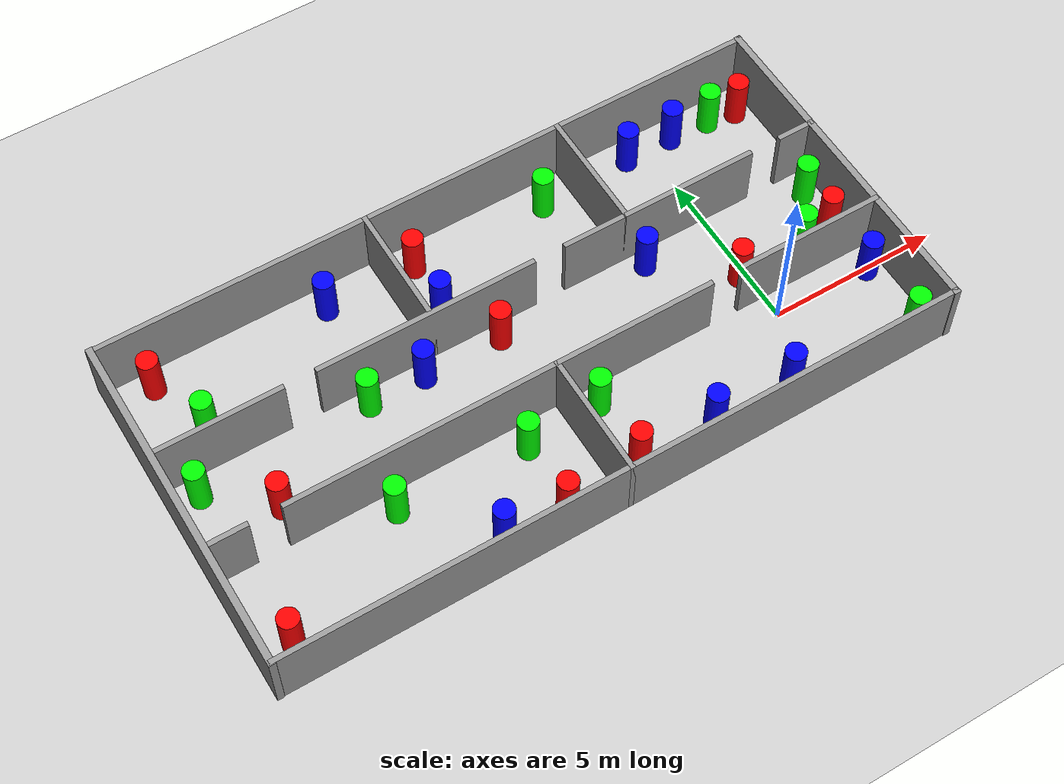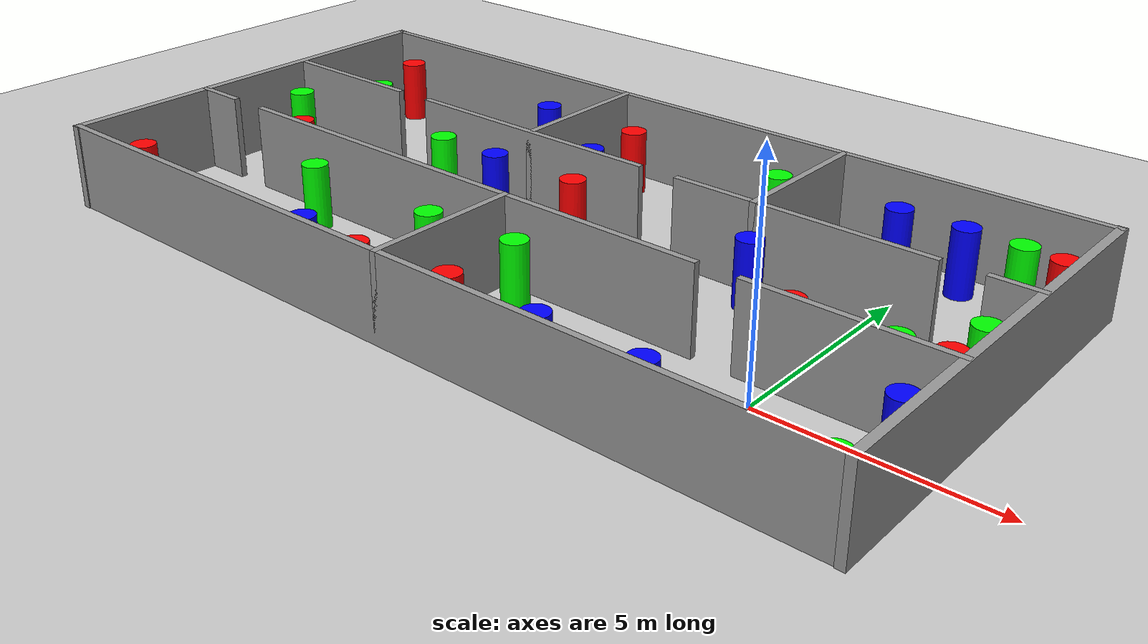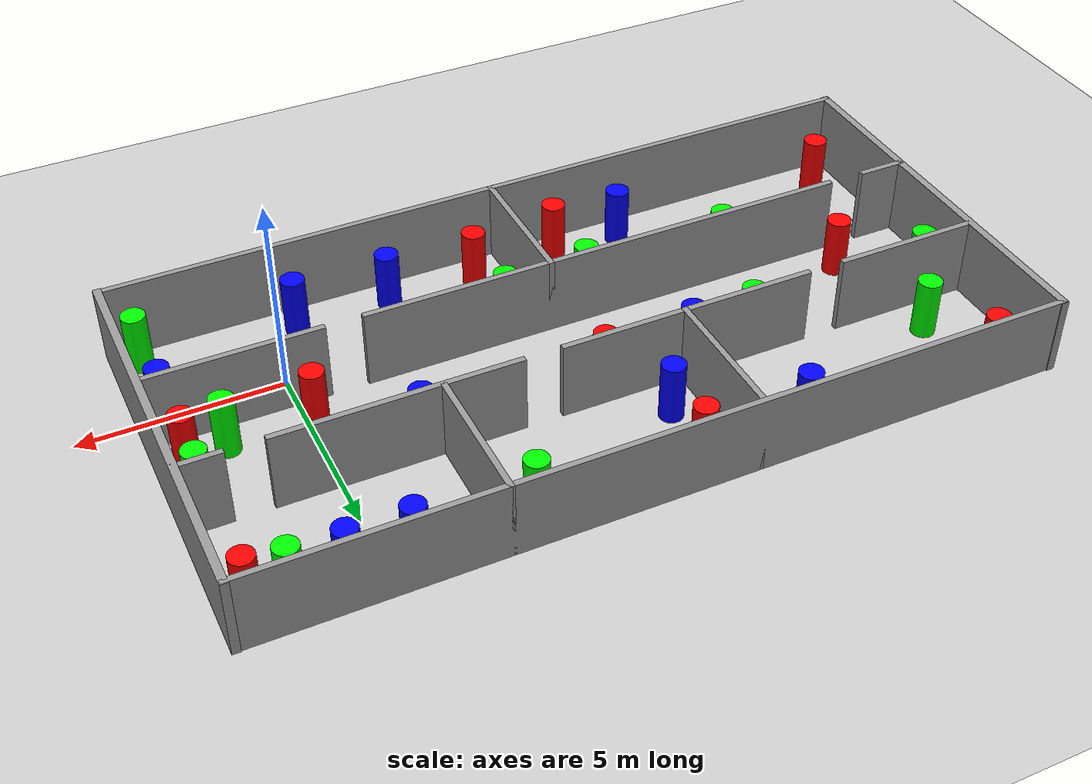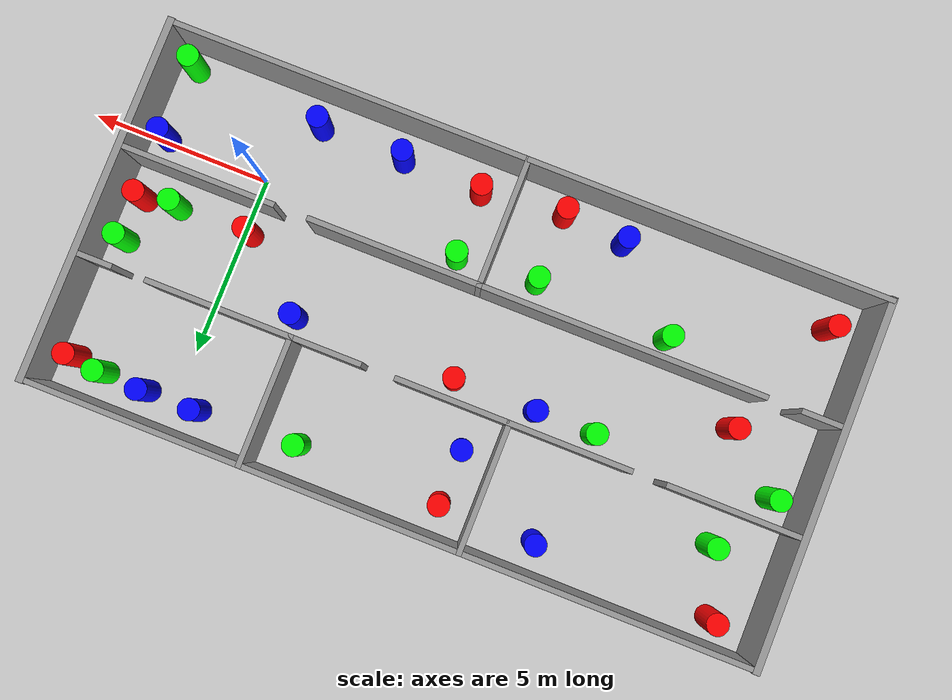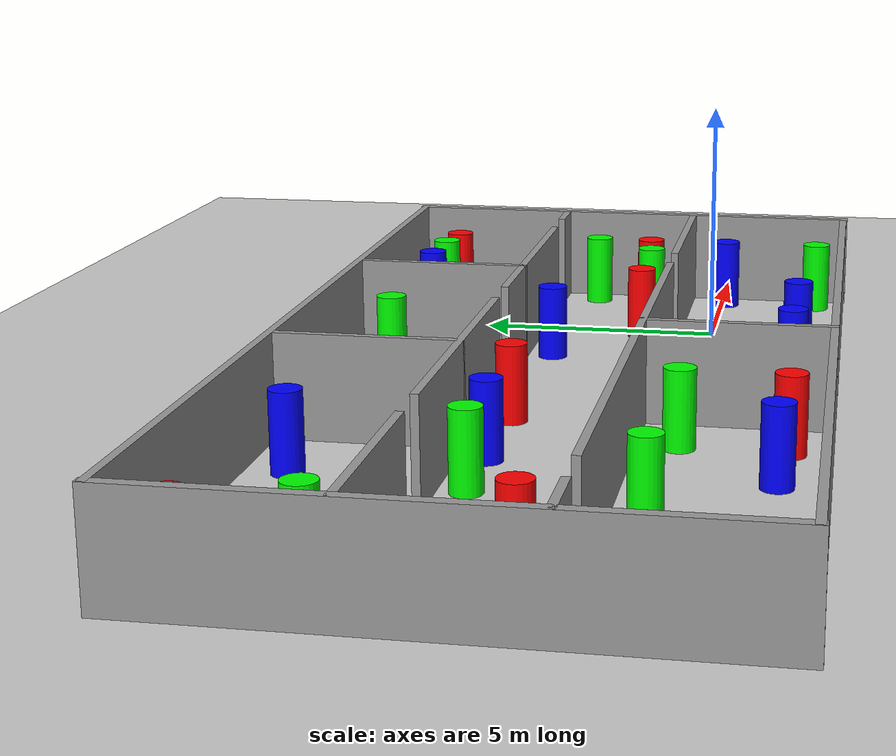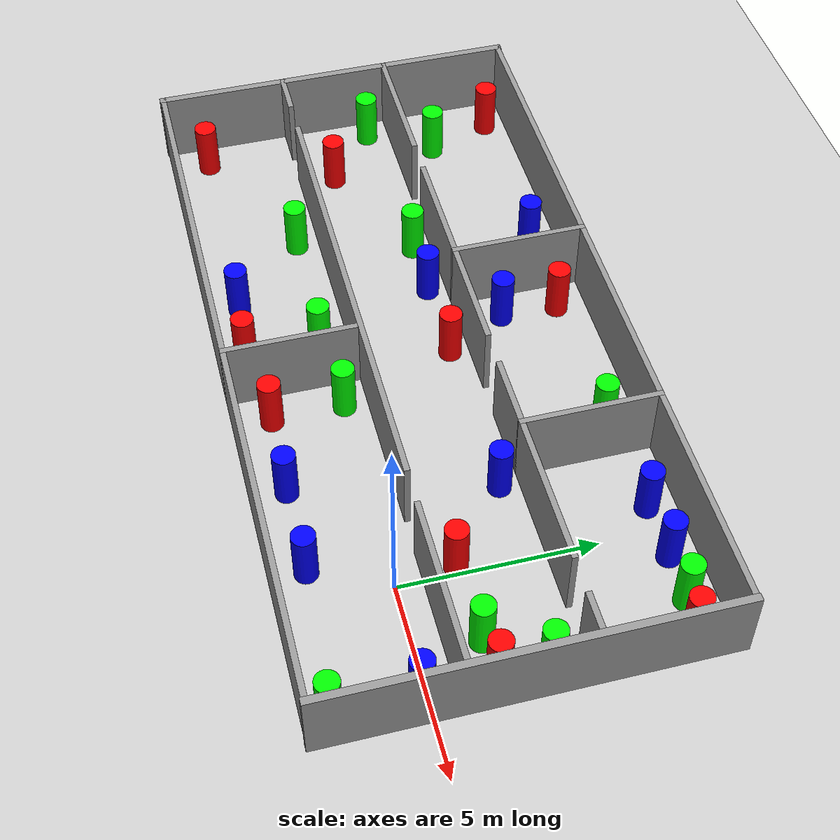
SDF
<sdf version="1.6">
 <world name="default">
  <light name="sun" type="directional">
   <pose>0 0 10 0 -0 0</pose>
   <diffuse>0.8 0.8 0.8 1</diffuse>
   <specular>0.2 0.2 0.2 1</specular>
   <attenuation>
    <range>1000</range>
    <constant>0.9</constant>
    <linear>0.01</linear>
    <quadratic>0.001</quadratic>
   </attenuation>
   <direction>-0.5 0.1 -0.9</direction>
  </light>
  <model name="ground_plane">
   <static>1</static>
   <link name="link">
    <collision name="collision">
     <geometry><plane><normal>0 0 1</normal><size>100 100</size></plane></geometry>
     <surface>
      <contact><collide_bitmask>65535</collide_bitmask></contact>
      <friction><ode><mu>100</mu><mu2>50</mu2></ode></friction>
     </surface>
    </collision>
    <visual name="visual">
     <cast_shadows>0</cast_shadows>
     <geometry><plane><normal>0 0 1</normal><size>100 100</size></plane></geometry>
     <material>
      <script><uri>file://media/materials/scripts/gazebo.material</uri><name>Gazebo/Grey</name></script>
     </material>
    </visual>
   </link>
  </model>
  <gravity>0 0 -9.8</gravity>
  <magnetic_field>6e-06 2.3e-05 -4.2e-05</magnetic_field>
  <atmosphere type="adiabatic"/>
  <physics name="default_physics" default="0" type="ode">
   <max_step_size>0.001</max_step_size>
   <real_time_factor>1</real_time_factor>
   <real_time_update_rate>1000</real_time_update_rate>
  </physics>
  <scene><ambient>0.4 0.4 0.4 1</ambient><background>0.7 0.7 0.7 1</background><shadows>1</shadows></scene>
  <spherical_coordinates>
   <surface_model>EARTH_WGS84</surface_model>
   <latitude_deg>0</latitude_deg>
   <longitude_deg>0</longitude_deg>
   <elevation>0</elevation>
   <heading_deg>0</heading_deg>
  </spherical_coordinates>
  <model name="indoor1">
   <pose>-6.52396 2.25289 0 0 -0 0</pose>
   <link name="Wall_17">
    <pose>0 -1.5 0 0 -0 0</pose>
    <visual name="Wall_17_Visual_0">
     <pose>-9.43386 0 1 0 -0 0</pose>
     <geometry><box><size>1.28227 0.15 2</size></box></geometry>
     <material>
      <script><uri>file://media/materials/scripts/gazebo.material</uri><name>Gazebo/Grey</name></script>
      <ambient>1 1 1 1</ambient>
     </material>
     <meta><layer>0</layer></meta>
    </visual>
    <collision name="Wall_17_Collision_0">
     <geometry><box><size>1.28227 0.15 2</size></box></geometry>
     <pose>-9.43386 0 1 0 -0 0</pose>
    </collision>
    <visual name="Wall_17_Visual_1">
     <pose>-1.56699 0 1 0 -0 0</pose>
     <geometry><box><size>12.6515 0.15 2</size></box></geometry>
     <material>
      <script><uri>file://media/materials/scripts/gazebo.material</uri><name>Gazebo/Grey</name></script>
      <ambient>1 1 1 1</ambient>
     </material>
     <meta><layer>0</layer></meta>
    </visual>
    <collision name="Wall_17_Collision_1">
     <geometry><box><size>12.6515 0.15 2</size></box></geometry>
     <pose>-1.56699 0 1 0 -0 0</pose>
    </collision>
    <visual name="Wall_17_Visual_2">
     <pose>7.86687 0 1 0 -0 0</pose>
     <geometry><box><size>4.41625 0.15 2</size></box></geometry>
     <material>
      <script><uri>file://media/materials/scripts/gazebo.material</uri><name>Gazebo/Grey</name></script>
      <ambient>1 1 1 1</ambient>
     </material>
     <meta><layer>0</layer></meta>
    </visual>
    <collision name="Wall_17_Collision_2">
     <geometry><box><size>4.41625 0.15 2</size></box></geometry>
     <pose>7.86687 0 1 0 -0 0</pose>
    </collision>
   </link>
   <link name="Wall_19">
    <pose>0 1.5 0 0 -0 0</pose>
    <visual name="Wall_19_Visual_0">
     <pose>-8.16437 0 1 0 -0 0</pose>
     <geometry><box><size>3.82126 0.15 2</size></box></geometry>
     <material>
      <script><uri>file://media/materials/scripts/gazebo.material</uri><name>Gazebo/Grey</name></script>
      <ambient>1 1 1 1</ambient>
     </material>
     <meta><layer>0</layer></meta>
    </visual>
    <collision name="Wall_19_Collision_0">
     <geometry><box><size>3.82126 0.15 2</size></box></geometry>
     <pose>-8.16437 0 1 0 -0 0</pose>
    </collision>
    <visual name="Wall_19_Visual_1">
     <pose>-2.10232 0 1 0 -0 0</pose>
     <geometry><box><size>6.50284 0.15 2</size></box></geometry>
     <material>
      <script><uri>file://media/materials/scripts/gazebo.material</uri><name>Gazebo/Grey</name></script>
      <ambient>1 1 1 1</ambient>
     </material>
     <meta><layer>0</layer></meta>
    </visual>
    <collision name="Wall_19_Collision_1">
     <geometry><box><size>6.50284 0.15 2</size></box></geometry>
     <pose>-2.10232 0 1 0 -0 0</pose>
    </collision>
    <visual name="Wall_19_Visual_2">
     <pose>5.0405 0 1 0 -0 0</pose>
     <geometry><box><size>5.9828 0.15 2</size></box></geometry>
     <material>
      <script><uri>file://media/materials/scripts/gazebo.material</uri><name>Gazebo/Grey</name></script>
      <ambient>1 1 1 1</ambient>
     </material>
     <meta><layer>0</layer></meta>
    </visual>
    <collision name="Wall_19_Collision_2">
     <geometry><box><size>5.9828 0.15 2</size></box></geometry>
     <pose>5.0405 0 1 0 -0 0</pose>
    </collision>
    <visual name="Wall_19_Visual_3">
     <pose>9.50345 0 1 0 -0 0</pose>
     <geometry><box><size>1.1431 0.15 2</size></box></geometry>
     <material>
      <script><uri>file://media/materials/scripts/gazebo.material</uri><name>Gazebo/Grey</name></script>
      <ambient>1 1 1 1</ambient>
     </material>
     <meta><layer>0</layer></meta>
    </visual>
    <collision name="Wall_19_Collision_3">
     <geometry><box><size>1.1431 0.15 2</size></box></geometry>
     <pose>9.50345 0 1 0 -0 0</pose>
    </collision>
   </link>
   <link name="Wall_21">
    <collision name="Wall_21_Collision">
     <geometry><box><size>3.65 0.15 2</size></box></geometry>
     <pose>0 0 1 0 -0 0</pose>
    </collision>
    <visual name="Wall_21_Visual">
     <pose>0 0 1 0 -0 0</pose>
     <geometry><box><size>3.65 0.15 2</size></box></geometry>
     <material>
      <script><uri>file://media/materials/scripts/gazebo.material</uri><name>Gazebo/Grey</name></script>
      <ambient>1 1 1 1</ambient>
     </material>
     <meta><layer>0</layer></meta>
    </visual>
    <pose>-2 3.25 0 0 -0 1.5708</pose>
   </link>
   <link name="Wall_23">
    <collision name="Wall_23_Collision">
     <geometry><box><size>3.65 0.15 2</size></box></geometry>
     <pose>0 0 1 0 -0 0</pose>
    </collision>
    <visual name="Wall_23_Visual">
     <pose>0 0 1 0 -0 0</pose>
     <geometry><box><size>3.65 0.15 2</size></box></geometry>
     <material>
      <script><uri>file://media/materials/scripts/gazebo.material</uri><name>Gazebo/Grey</name></script>
      <ambient>1 1 1 1</ambient>
     </material>
     <meta><layer>0</layer></meta>
    </visual>
    <pose>4 3.25 0 0 -0 1.5708</pose>
   </link>
   <link name="Wall_25">
    <collision name="Wall_25_Collision">
     <geometry><box><size>3.65 0.15 2</size></box></geometry>
     <pose>0 0 1 0 -0 0</pose>
    </collision>
    <visual name="Wall_25_Visual">
     <pose>0 0 1 0 -0 0</pose>
     <geometry><box><size>3.65 0.15 2</size></box></geometry>
     <material>
      <script><uri>file://media/materials/scripts/gazebo.material</uri><name>Gazebo/Grey</name></script>
      <ambient>1 1 1 1</ambient>
     </material>
     <meta><layer>0</layer></meta>
    </visual>
    <pose>0 -3.25 0 0 -0 1.5708</pose>
   </link>
   <link name="Wall_5">
    <collision name="Wall_5_Collision">
     <geometry><box><size>20.15 0.15 2</size></box></geometry>
     <pose>0 0 1 0 -0 0</pose>
    </collision>
    <visual name="Wall_5_Visual">
     <pose>0 0 1 0 -0 0</pose>
     <geometry><box><size>20.15 0.15 2</size></box></geometry>
     <material>
      <script><uri>file://media/materials/scripts/gazebo.material</uri><name>Gazebo/Grey</name></script>
      <ambient>1 1 1 1</ambient>
     </material>
     <meta><layer>0</layer></meta>
    </visual>
    <pose>0 5 0 0 -0 0</pose>
   </link>
   <link name="Wall_6">
    <collision name="Wall_6_Collision">
     <geometry><box><size>10.2 0.2 2</size></box></geometry>
     <pose>0 0 1 0 -0 0</pose>
    </collision>
    <visual name="Wall_6_Visual">
     <pose>0 0 1 0 -0 0</pose>
     <geometry><box><size>10.2 0.2 2</size></box></geometry>
     <material>
      <script><uri>file://media/materials/scripts/gazebo.material</uri><name>Gazebo/Grey</name></script>
      <ambient>1 1 1 1</ambient>
     </material>
     <meta><layer>0</layer></meta>
    </visual>
    <pose>10 0 0 0 0 -1.5708</pose>
   </link>
   <link name="Wall_7">
    <collision name="Wall_7_Collision">
     <geometry><box><size>20.15 0.15 2</size></box></geometry>
     <pose>0 0 1 0 -0 0</pose>
    </collision>
    <visual name="Wall_7_Visual">
     <pose>0 0 1 0 -0 0</pose>
     <geometry><box><size>20.15 0.15 2</size></box></geometry>
     <material>
      <script><uri>file://media/materials/scripts/gazebo.material</uri><name>Gazebo/Grey</name></script>
      <ambient>1 1 1 1</ambient>
     </material>
     <meta><layer>0</layer></meta>
    </visual>
    <pose>0 -5 0 0 -0 3.14159</pose>
   </link>
   <link name="Wall_8">
    <collision name="Wall_8_Collision">
     <geometry><box><size>10.2 0.2 2</size></box></geometry>
     <pose>0 0 1 0 -0 0</pose>
    </collision>
    <visual name="Wall_8_Visual">
     <pose>0 0 1 0 -0 0</pose>
     <geometry><box><size>10.2 0.2 2</size></box></geometry>
     <material>
      <script><uri>file://media/materials/scripts/gazebo.material</uri><name>Gazebo/Grey</name></script>
      <ambient>1 1 1 1</ambient>
     </material>
     <meta><layer>0</layer></meta>
    </visual>
    <pose>-10 0 0 0 -0 1.5708</pose>
   </link>
   <static>1</static>
  </model>
  <model name="class01">
   <link name="link">
    <pose>-0.202221 0.506091 0 0 -0 0</pose>
    <inertial>
     <mass>1</mass>
     <inertia><ixx>0.145833</ixx><ixy>0</ixy><ixz>0</ixz><iyy>0.145833</iyy><iyz>0</iyz><izz>0.125</izz></inertia>
    </inertial>
    <visual name="visual">
     <geometry><cylinder><radius>0.3</radius><length>2</length></cylinder></geometry>
     <material>
      <script><name>Gazebo/Grey</name><uri>file://media/materials/scripts/gazebo.material</uri></script>
      <ambient>1 0 0 1</ambient>
      <diffuse>0.7 0.7 0.7 1</diffuse>
      <specular>0.01 0.01 0.01 1</specular>
      <emissive>0 0 0 1</emissive>
      <shader type="vertex"><normal_map>__default__</normal_map></shader>
     </material>
    </visual>
    <collision name="collision">
     <geometry><cylinder><radius>0.5</radius><length>1</length></cylinder></geometry>
     <surface>
      <friction>
       <ode><mu>1</mu><mu2>1</mu2><fdir1>0 0 0</fdir1><slip1>0</slip1><slip2>0</slip2></ode>
       <torsional>
        <coefficient>1</coefficient>
        <patch_radius>0</patch_radius>
        <surface_radius>0</surface_radius>
        <use_patch_radius>1</use_patch_radius>
        <ode><slip>0</slip></ode>
       </torsional>
      </friction>
      <bounce><restitution_coefficient>0</restitution_coefficient><threshold>1e+06</threshold></bounce>
      <contact>
       <collide_without_contact>0</collide_without_contact>
       <collide_without_contact_bitmask>1</collide_without_contact_bitmask>
       <collide_bitmask>1</collide_bitmask>
       <ode>
        <soft_cfm>0</soft_cfm>
        <soft_erp>0.2</soft_erp>
        <kp>1e+13</kp>
        <kd>1</kd>
        <max_vel>0.01</max_vel>
        <min_depth>0</min_depth>
       </ode>
       <bullet>
        <split_impulse>1</split_impulse>
        <split_impulse_penetration_threshold>-0.01</split_impulse_penetration_threshold>
        <soft_cfm>0</soft_cfm>
        <soft_erp>0.2</soft_erp>
        <kp>1e+13</kp>
        <kd>1</kd>
       </bullet>
      </contact>
     </surface>
    </collision>
   </link>
   <static>0</static>
   <pose>-15.3971 -2.24481 0.5 0 -0 0</pose>
  </model>
  <model name="class01_clone">
   <link name="link">
    <pose>-0.202221 0.506091 0 0 -0 0</pose>
    <inertial>
     <mass>1</mass>
     <inertia><ixx>0.145833</ixx><ixy>0</ixy><ixz>0</ixz><iyy>0.145833</iyy><iyz>0</iyz><izz>0.125</izz></inertia>
    </inertial>
    <visual name="visual">
     <geometry><cylinder><radius>0.3</radius><length>2</length></cylinder></geometry>
     <material>
      <script><name>Gazebo/Grey</name><uri>file://media/materials/scripts/gazebo.material</uri></script>
      <ambient>1 0 0 1</ambient>
      <diffuse>0.7 0.7 0.7 1</diffuse>
      <specular>0.01 0.01 0.01 1</specular>
      <emissive>0 0 0 1</emissive>
      <shader type="vertex"><normal_map>__default__</normal_map></shader>
     </material>
    </visual>
    <collision name="collision">
     <geometry><cylinder><radius>0.5</radius><length>1</length></cylinder></geometry>
     <surface>
      <friction>
       <ode><mu>1</mu><mu2>1</mu2><fdir1>0 0 0</fdir1><slip1>0</slip1><slip2>0</slip2></ode>
       <torsional>
        <coefficient>1</coefficient>
        <patch_radius>0</patch_radius>
        <surface_radius>0</surface_radius>
        <use_patch_radius>1</use_patch_radius>
        <ode><slip>0</slip></ode>
       </torsional>
      </friction>
      <bounce><restitution_coefficient>0</restitution_coefficient><threshold>1e+06</threshold></bounce>
      <contact>
       <collide_without_contact>0</collide_without_contact>
       <collide_without_contact_bitmask>1</collide_without_contact_bitmask>
       <collide_bitmask>1</collide_bitmask>
       <ode>
        <soft_cfm>0</soft_cfm>
        <soft_erp>0.2</soft_erp>
        <kp>1e+13</kp>
        <kd>1</kd>
        <max_vel>0.01</max_vel>
        <min_depth>0</min_depth>
       </ode>
       <bullet>
        <split_impulse>1</split_impulse>
        <split_impulse_penetration_threshold>-0.01</split_impulse_penetration_threshold>
        <soft_cfm>0</soft_cfm>
        <soft_erp>0.2</soft_erp>
        <kp>1e+13</kp>
        <kd>1</kd>
       </bullet>
      </contact>
     </surface>
    </collision>
   </link>
   <static>0</static>
   <pose>-7.73161 -2.5534 0.499994 -3e-06 -1e-06 -0</pose>
  </model>
  <model name="class01_clone_0">
   <link name="link">
    <pose>-0.202221 0.506091 0 0 -0 0</pose>
    <inertial>
     <mass>1</mass>
     <inertia><ixx>0.145833</ixx><ixy>0</ixy><ixz>0</ixz><iyy>0.145833</iyy><iyz>0</iyz><izz>0.125</izz></inertia>
    </inertial>
    <visual name="visual">
     <geometry><cylinder><radius>0.3</radius><length>2</length></cylinder></geometry>
     <material>
      <script><name>Gazebo/Grey</name><uri>file://media/materials/scripts/gazebo.material</uri></script>
      <ambient>1 0 0 1</ambient>
      <diffuse>0.7 0.7 0.7 1</diffuse>
      <specular>0.01 0.01 0.01 1</specular>
      <emissive>0 0 0 1</emissive>
      <shader type="vertex"><normal_map>__default__</normal_map></shader>
     </material>
    </visual>
    <collision name="collision">
     <geometry><cylinder><radius>0.5</radius><length>1</length></cylinder></geometry>
     <surface>
      <friction>
       <ode><mu>1</mu><mu2>1</mu2><fdir1>0 0 0</fdir1><slip1>0</slip1><slip2>0</slip2></ode>
       <torsional>
        <coefficient>1</coefficient>
        <patch_radius>0</patch_radius>
        <surface_radius>0</surface_radius>
        <use_patch_radius>1</use_patch_radius>
        <ode><slip>0</slip></ode>
       </torsional>
      </friction>
      <bounce><restitution_coefficient>0</restitution_coefficient><threshold>1e+06</threshold></bounce>
      <contact>
       <collide_without_contact>0</collide_without_contact>
       <collide_without_contact_bitmask>1</collide_without_contact_bitmask>
       <collide_bitmask>1</collide_bitmask>
       <ode>
        <soft_cfm>0</soft_cfm>
        <soft_erp>0.2</soft_erp>
        <kp>1e+13</kp>
        <kd>1</kd>
        <max_vel>0.01</max_vel>
        <min_depth>0</min_depth>
       </ode>
       <bullet>
        <split_impulse>1</split_impulse>
        <split_impulse_penetration_threshold>-0.01</split_impulse_penetration_threshold>
        <soft_cfm>0</soft_cfm>
        <soft_erp>0.2</soft_erp>
        <kp>1e+13</kp>
        <kd>1</kd>
       </bullet>
      </contact>
     </surface>
    </collision>
   </link>
   <static>0</static>
   <pose>-5.40307 -2.30982 0.499994 -3e-06 -1e-06 -0</pose>
  </model>
  <model name="class01_clone_2">
   <link name="link">
    <pose>-0.202221 0.506091 0 0 -0 0</pose>
    <inertial>
     <mass>1</mass>
     <inertia><ixx>0.145833</ixx><ixy>0</ixy><ixz>0</ixz><iyy>0.145833</iyy><iyz>0</iyz><izz>0.125</izz></inertia>
    </inertial>
    <visual name="visual">
     <geometry><cylinder><radius>0.3</radius><length>2</length></cylinder></geometry>
     <material>
      <script><name>Gazebo/Grey</name><uri>file://media/materials/scripts/gazebo.material</uri></script>
      <ambient>1 0 0 1</ambient>
      <diffuse>0.7 0.7 0.7 1</diffuse>
      <specular>0.01 0.01 0.01 1</specular>
      <emissive>0 0 0 1</emissive>
      <shader type="vertex"><normal_map>__default__</normal_map></shader>
     </material>
    </visual>
    <collision name="collision">
     <geometry><cylinder><radius>0.5</radius><length>1</length></cylinder></geometry>
     <surface>
      <friction>
       <ode><mu>1</mu><mu2>1</mu2><fdir1>0 0 0</fdir1><slip1>0</slip1><slip2>0</slip2></ode>
       <torsional>
        <coefficient>1</coefficient>
        <patch_radius>0</patch_radius>
        <surface_radius>0</surface_radius>
        <use_patch_radius>1</use_patch_radius>
        <ode><slip>0</slip></ode>
       </torsional>
      </friction>
      <bounce><restitution_coefficient>0</restitution_coefficient><threshold>1e+06</threshold></bounce>
      <contact>
       <collide_without_contact>0</collide_without_contact>
       <collide_without_contact_bitmask>1</collide_without_contact_bitmask>
       <collide_bitmask>1</collide_bitmask>
       <ode>
        <soft_cfm>0</soft_cfm>
        <soft_erp>0.2</soft_erp>
        <kp>1e+13</kp>
        <kd>1</kd>
        <max_vel>0.01</max_vel>
        <min_depth>0</min_depth>
       </ode>
       <bullet>
        <split_impulse>1</split_impulse>
        <split_impulse_penetration_threshold>-0.01</split_impulse_penetration_threshold>
        <soft_cfm>0</soft_cfm>
        <soft_erp>0.2</soft_erp>
        <kp>1e+13</kp>
        <kd>1</kd>
       </bullet>
      </contact>
     </surface>
    </collision>
   </link>
   <static>0</static>
   <pose>-15.1319 6.07169 0.499994 -3e-06 -1e-06 -0</pose>
  </model>
  <model name="class01_clone_3">
   <link name="link">
    <pose>-0.202221 0.506091 0 0 -0 0</pose>
    <inertial>
     <mass>1</mass>
     <inertia><ixx>0.145833</ixx><ixy>0</ixy><ixz>0</ixz><iyy>0.145833</iyy><iyz>0</iyz><izz>0.125</izz></inertia>
    </inertial>
    <visual name="visual">
     <geometry><cylinder><radius>0.3</radius><length>2</length></cylinder></geometry>
     <material>
      <script><name>Gazebo/Grey</name><uri>file://media/materials/scripts/gazebo.material</uri></script>
      <ambient>1 0 0 1</ambient>
      <diffuse>0.7 0.7 0.7 1</diffuse>
      <specular>0.01 0.01 0.01 1</specular>
      <emissive>0 0 0 1</emissive>
      <shader type="vertex"><normal_map>__default__</normal_map></shader>
     </material>
    </visual>
    <collision name="collision">
     <geometry><cylinder><radius>0.5</radius><length>1</length></cylinder></geometry>
     <surface>
      <friction>
       <ode><mu>1</mu><mu2>1</mu2><fdir1>0 0 0</fdir1><slip1>0</slip1><slip2>0</slip2></ode>
       <torsional>
        <coefficient>1</coefficient>
        <patch_radius>0</patch_radius>
        <surface_radius>0</surface_radius>
        <use_patch_radius>1</use_patch_radius>
        <ode><slip>0</slip></ode>
       </torsional>
      </friction>
      <bounce><restitution_coefficient>0</restitution_coefficient><threshold>1e+06</threshold></bounce>
      <contact>
       <collide_without_contact>0</collide_without_contact>
       <collide_without_contact_bitmask>1</collide_without_contact_bitmask>
       <collide_bitmask>1</collide_bitmask>
       <ode>
        <soft_cfm>0</soft_cfm>
        <soft_erp>0.2</soft_erp>
        <kp>1e+13</kp>
        <kd>1</kd>
        <max_vel>0.01</max_vel>
        <min_depth>0</min_depth>
       </ode>
       <bullet>
        <split_impulse>1</split_impulse>
        <split_impulse_penetration_threshold>-0.01</split_impulse_penetration_threshold>
        <soft_cfm>0</soft_cfm>
        <soft_erp>0.2</soft_erp>
        <kp>1e+13</kp>
        <kd>1</kd>
       </bullet>
      </contact>
     </surface>
    </collision>
   </link>
   <static>0</static>
   <pose>-7.4078 5.86584 0.499994 -3e-06 -1e-06 -0</pose>
  </model>
  <model name="class01_clone_4">
   <link name="link">
    <pose>-0.202221 0.506091 0 0 -0 0</pose>
    <inertial>
     <mass>1</mass>
     <inertia><ixx>0.145833</ixx><ixy>0</ixy><ixz>0</ixz><iyy>0.145833</iyy><iyz>0</iyz><izz>0.125</izz></inertia>
    </inertial>
    <visual name="visual">
     <geometry><cylinder><radius>0.3</radius><length>2</length></cylinder></geometry>
     <material>
      <script><name>Gazebo/Grey</name><uri>file://media/materials/scripts/gazebo.material</uri></script>
      <ambient>1 0 0 1</ambient>
      <diffuse>0.7 0.7 0.7 1</diffuse>
      <specular>0.01 0.01 0.01 1</specular>
      <emissive>0 0 0 1</emissive>
      <shader type="vertex"><normal_map>__default__</normal_map></shader>
     </material>
    </visual>
    <collision name="collision">
     <geometry><cylinder><radius>0.5</radius><length>1</length></cylinder></geometry>
     <surface>
      <friction>
       <ode><mu>1</mu><mu2>1</mu2><fdir1>0 0 0</fdir1><slip1>0</slip1><slip2>0</slip2></ode>
       <torsional>
        <coefficient>1</coefficient>
        <patch_radius>0</patch_radius>
        <surface_radius>0</surface_radius>
        <use_patch_radius>1</use_patch_radius>
        <ode><slip>0</slip></ode>
       </torsional>
      </friction>
      <bounce><restitution_coefficient>0</restitution_coefficient><threshold>1e+06</threshold></bounce>
      <contact>
       <collide_without_contact>0</collide_without_contact>
       <collide_without_contact_bitmask>1</collide_without_contact_bitmask>
       <collide_bitmask>1</collide_bitmask>
       <ode>
        <soft_cfm>0</soft_cfm>
        <soft_erp>0.2</soft_erp>
        <kp>1e+13</kp>
        <kd>1</kd>
        <max_vel>0.01</max_vel>
        <min_depth>0</min_depth>
       </ode>
       <bullet>
        <split_impulse>1</split_impulse>
        <split_impulse_penetration_threshold>-0.01</split_impulse_penetration_threshold>
        <soft_cfm>0</soft_cfm>
        <soft_erp>0.2</soft_erp>
        <kp>1e+13</kp>
        <kd>1</kd>
       </bullet>
      </contact>
     </surface>
    </collision>
   </link>
   <static>0</static>
   <pose>3.07826 5.78008 0.499995 -3e-06 -4e-06 -0</pose>
  </model>
  <model name="class01_clone_5">
   <link name="link">
    <pose>-0.202221 0.506091 0 0 -0 0</pose>
    <inertial>
     <mass>1</mass>
     <inertia><ixx>0.145833</ixx><ixy>0</ixy><ixz>0</ixz><iyy>0.145833</iyy><iyz>0</iyz><izz>0.125</izz></inertia>
    </inertial>
    <visual name="visual">
     <geometry><cylinder><radius>0.3</radius><length>2</length></cylinder></geometry>
     <material>
      <script><name>Gazebo/Grey</name><uri>file://media/materials/scripts/gazebo.material</uri></script>
      <ambient>1 0 0 1</ambient>
      <diffuse>0.7 0.7 0.7 1</diffuse>
      <specular>0.01 0.01 0.01 1</specular>
      <emissive>0 0 0 1</emissive>
      <shader type="vertex"><normal_map>__default__</normal_map></shader>
     </material>
    </visual>
    <collision name="collision">
     <geometry><cylinder><radius>0.5</radius><length>1</length></cylinder></geometry>
     <surface>
      <friction>
       <ode><mu>1</mu><mu2>1</mu2><fdir1>0 0 0</fdir1><slip1>0</slip1><slip2>0</slip2></ode>
       <torsional>
        <coefficient>1</coefficient>
        <patch_radius>0</patch_radius>
        <surface_radius>0</surface_radius>
        <use_patch_radius>1</use_patch_radius>
        <ode><slip>0</slip></ode>
       </torsional>
      </friction>
      <bounce><restitution_coefficient>0</restitution_coefficient><threshold>1e+06</threshold></bounce>
      <contact>
       <collide_without_contact>0</collide_without_contact>
       <collide_without_contact_bitmask>1</collide_without_contact_bitmask>
       <collide_bitmask>1</collide_bitmask>
       <ode>
        <soft_cfm>0</soft_cfm>
        <soft_erp>0.2</soft_erp>
        <kp>1e+13</kp>
        <kd>1</kd>
        <max_vel>0.01</max_vel>
        <min_depth>0</min_depth>
       </ode>
       <bullet>
        <split_impulse>1</split_impulse>
        <split_impulse_penetration_threshold>-0.01</split_impulse_penetration_threshold>
        <soft_cfm>0</soft_cfm>
        <soft_erp>0.2</soft_erp>
        <kp>1e+13</kp>
        <kd>1</kd>
       </bullet>
      </contact>
     </surface>
    </collision>
   </link>
   <static>0</static>
   <pose>-13.9099 1.19095 0.499994 -3e-06 -1e-06 -0</pose>
  </model>
  <model name="class01_clone_6">
   <link name="link">
    <pose>-0.202221 0.506091 0 0 -0 0</pose>
    <inertial>
     <mass>1</mass>
     <inertia><ixx>0.145833</ixx><ixy>0</ixy><ixz>0</ixz><iyy>0.145833</iyy><iyz>0</iyz><izz>0.125</izz></inertia>
    </inertial>
    <visual name="visual">
     <geometry><cylinder><radius>0.3</radius><length>2</length></cylinder></geometry>
     <material>
      <script><name>Gazebo/Grey</name><uri>file://media/materials/scripts/gazebo.material</uri></script>
      <ambient>1 0 0 1</ambient>
      <diffuse>0.7 0.7 0.7 1</diffuse>
      <specular>0.01 0.01 0.01 1</specular>
      <emissive>0 0 0 1</emissive>
      <shader type="vertex"><normal_map>__default__</normal_map></shader>
     </material>
    </visual>
    <collision name="collision">
     <geometry><cylinder><radius>0.5</radius><length>1</length></cylinder></geometry>
     <surface>
      <friction>
       <ode><mu>1</mu><mu2>1</mu2><fdir1>0 0 0</fdir1><slip1>0</slip1><slip2>0</slip2></ode>
       <torsional>
        <coefficient>1</coefficient>
        <patch_radius>0</patch_radius>
        <surface_radius>0</surface_radius>
        <use_patch_radius>1</use_patch_radius>
        <ode><slip>0</slip></ode>
       </torsional>
      </friction>
      <bounce><restitution_coefficient>0</restitution_coefficient><threshold>1e+06</threshold></bounce>
      <contact>
       <collide_without_contact>0</collide_without_contact>
       <collide_without_contact_bitmask>1</collide_without_contact_bitmask>
       <collide_bitmask>1</collide_bitmask>
       <ode>
        <soft_cfm>0</soft_cfm>
        <soft_erp>0.2</soft_erp>
        <kp>1e+13</kp>
        <kd>1</kd>
        <max_vel>0.01</max_vel>
        <min_depth>0</min_depth>
       </ode>
       <bullet>
        <split_impulse>1</split_impulse>
        <split_impulse_penetration_threshold>-0.01</split_impulse_penetration_threshold>
        <soft_cfm>0</soft_cfm>
        <soft_erp>0.2</soft_erp>
        <kp>1e+13</kp>
        <kd>1</kd>
       </bullet>
      </contact>
     </surface>
    </collision>
   </link>
   <static>0</static>
   <pose>-6.57558 2.67179 0.499996 3e-06 1e-06 -0</pose>
  </model>
  <model name="class01_clone_7">
   <link name="link">
    <pose>-0.202221 0.506091 0 0 -0 0</pose>
    <inertial>
     <mass>1</mass>
     <inertia><ixx>0.145833</ixx><ixy>0</ixy><ixz>0</ixz><iyy>0.145833</iyy><iyz>0</iyz><izz>0.125</izz></inertia>
    </inertial>
    <visual name="visual">
     <geometry><cylinder><radius>0.3</radius><length>2</length></cylinder></geometry>
     <material>
      <script><name>Gazebo/Grey</name><uri>file://media/materials/scripts/gazebo.material</uri></script>
      <ambient>1 0 0 1</ambient>
      <diffuse>0.7 0.7 0.7 1</diffuse>
      <specular>0.01 0.01 0.01 1</specular>
      <emissive>0 0 0 1</emissive>
      <shader type="vertex"><normal_map>__default__</normal_map></shader>
     </material>
    </visual>
    <collision name="collision">
     <geometry><cylinder><radius>0.5</radius><length>1</length></cylinder></geometry>
     <surface>
      <friction>
       <ode><mu>1</mu><mu2>1</mu2><fdir1>0 0 0</fdir1><slip1>0</slip1><slip2>0</slip2></ode>
       <torsional>
        <coefficient>1</coefficient>
        <patch_radius>0</patch_radius>
        <surface_radius>0</surface_radius>
        <use_patch_radius>1</use_patch_radius>
        <ode><slip>0</slip></ode>
       </torsional>
      </friction>
      <bounce><restitution_coefficient>0</restitution_coefficient><threshold>1e+06</threshold></bounce>
      <contact>
       <collide_without_contact>0</collide_without_contact>
       <collide_without_contact_bitmask>1</collide_without_contact_bitmask>
       <collide_bitmask>1</collide_bitmask>
       <ode>
        <soft_cfm>0</soft_cfm>
        <soft_erp>0.2</soft_erp>
        <kp>1e+13</kp>
        <kd>1</kd>
        <max_vel>0.01</max_vel>
        <min_depth>0</min_depth>
       </ode>
       <bullet>
        <split_impulse>1</split_impulse>
        <split_impulse_penetration_threshold>-0.01</split_impulse_penetration_threshold>
        <soft_cfm>0</soft_cfm>
        <soft_erp>0.2</soft_erp>
        <kp>1e+13</kp>
        <kd>1</kd>
       </bullet>
      </contact>
     </surface>
    </collision>
   </link>
   <static>0</static>
   <pose>-0.021381 1.02694 0.499996 3e-06 1e-06 -0</pose>
  </model>
  <model name="class01_clone_8">
   <link name="link">
    <pose>-0.202221 0.506091 0 0 -0 0</pose>
    <inertial>
     <mass>1</mass>
     <inertia><ixx>0.145833</ixx><ixy>0</ixy><ixz>0</ixz><iyy>0.145833</iyy><iyz>0</iyz><izz>0.125</izz></inertia>
    </inertial>
    <visual name="visual">
     <geometry><cylinder><radius>0.3</radius><length>2</length></cylinder></geometry>
     <material>
      <script><name>Gazebo/Grey</name><uri>file://media/materials/scripts/gazebo.material</uri></script>
      <ambient>1 0 0 1</ambient>
      <diffuse>0.7 0.7 0.7 1</diffuse>
      <specular>0.01 0.01 0.01 1</specular>
      <emissive>0 0 0 1</emissive>
      <shader type="vertex"><normal_map>__default__</normal_map></shader>
     </material>
    </visual>
    <collision name="collision">
     <geometry><cylinder><radius>0.5</radius><length>1</length></cylinder></geometry>
     <surface>
      <friction>
       <ode><mu>1</mu><mu2>1</mu2><fdir1>0 0 0</fdir1><slip1>0</slip1><slip2>0</slip2></ode>
       <torsional>
        <coefficient>1</coefficient>
        <patch_radius>0</patch_radius>
        <surface_radius>0</surface_radius>
        <use_patch_radius>1</use_patch_radius>
        <ode><slip>0</slip></ode>
       </torsional>
      </friction>
      <bounce><restitution_coefficient>0</restitution_coefficient><threshold>1e+06</threshold></bounce>
      <contact>
       <collide_without_contact>0</collide_without_contact>
       <collide_without_contact_bitmask>1</collide_without_contact_bitmask>
       <collide_bitmask>1</collide_bitmask>
       <ode>
        <soft_cfm>0</soft_cfm>
        <soft_erp>0.2</soft_erp>
        <kp>1e+13</kp>
        <kd>1</kd>
        <max_vel>0.01</max_vel>
        <min_depth>0</min_depth>
       </ode>
       <bullet>
        <split_impulse>1</split_impulse>
        <split_impulse_penetration_threshold>-0.01</split_impulse_penetration_threshold>
        <soft_cfm>0</soft_cfm>
        <soft_erp>0.2</soft_erp>
        <kp>1e+13</kp>
        <kd>1</kd>
       </bullet>
      </contact>
     </surface>
    </collision>
   </link>
   <static>0</static>
   <pose>3.0328 1.17628 0.499996 3e-06 1e-06 -0</pose>
  </model>
  <model name="class02">
   <link name="link">
    <inertial>
     <mass>1</mass>
     <inertia><ixx>0.145833</ixx><ixy>0</ixy><ixz>0</ixz><iyy>0.145833</iyy><iyz>0</iyz><izz>0.125</izz></inertia>
    </inertial>
    <visual name="visual">
     <geometry><cylinder><radius>0.3</radius><length>2</length></cylinder></geometry>
     <material>
      <script><name>Gazebo/Grey</name><uri>file://media/materials/scripts/gazebo.material</uri></script>
      <ambient>0 1 0 1</ambient>
      <diffuse>0.7 0.7 0.7 1</diffuse>
      <specular>0.01 0.01 0.01 1</specular>
      <emissive>0 0 0 1</emissive>
      <shader type="vertex"><normal_map>__default__</normal_map></shader>
     </material>
    </visual>
    <collision name="collision">
     <geometry><cylinder><radius>0.5</radius><length>1</length></cylinder></geometry>
     <surface>
      <friction>
       <ode><mu>1</mu><mu2>1</mu2><fdir1>0 0 0</fdir1><slip1>0</slip1><slip2>0</slip2></ode>
       <torsional>
        <coefficient>1</coefficient>
        <patch_radius>0</patch_radius>
        <surface_radius>0</surface_radius>
        <use_patch_radius>1</use_patch_radius>
        <ode><slip>0</slip></ode>
       </torsional>
      </friction>
      <bounce><restitution_coefficient>0</restitution_coefficient><threshold>1e+06</threshold></bounce>
      <contact>
       <collide_without_contact>0</collide_without_contact>
       <collide_without_contact_bitmask>1</collide_without_contact_bitmask>
       <collide_bitmask>1</collide_bitmask>
       <ode>
        <soft_cfm>0</soft_cfm>
        <soft_erp>0.2</soft_erp>
        <kp>1e+13</kp>
        <kd>1</kd>
        <max_vel>0.01</max_vel>
        <min_depth>0</min_depth>
       </ode>
       <bullet>
        <split_impulse>1</split_impulse>
        <split_impulse_penetration_threshold>-0.01</split_impulse_penetration_threshold>
        <soft_cfm>0</soft_cfm>
        <soft_erp>0.2</soft_erp>
        <kp>1e+13</kp>
        <kd>1</kd>
       </bullet>
      </contact>
     </surface>
    </collision>
   </link>
   <static>0</static>
   <pose>-11.6766 0.078128 0.5 0 -0 0</pose>
  </model>
  <model name="class02_clone">
   <link name="link">
    <inertial>
     <mass>1</mass>
     <inertia><ixx>0.145833</ixx><ixy>0</ixy><ixz>0</ixz><iyy>0.145833</iyy><iyz>0</iyz><izz>0.125</izz></inertia>
    </inertial>
    <visual name="visual">
     <geometry><cylinder><radius>0.3</radius><length>2</length></cylinder></geometry>
     <material>
      <script><name>Gazebo/Grey</name><uri>file://media/materials/scripts/gazebo.material</uri></script>
      <ambient>0 1 0 1</ambient>
      <diffuse>0.7 0.7 0.7 1</diffuse>
      <specular>0.01 0.01 0.01 1</specular>
      <emissive>0 0 0 1</emissive>
      <shader type="vertex"><normal_map>__default__</normal_map></shader>
     </material>
    </visual>
    <collision name="collision">
     <geometry><cylinder><radius>0.5</radius><length>1</length></cylinder></geometry>
     <surface>
      <friction>
       <ode><mu>1</mu><mu2>1</mu2><fdir1>0 0 0</fdir1><slip1>0</slip1><slip2>0</slip2></ode>
       <torsional>
        <coefficient>1</coefficient>
        <patch_radius>0</patch_radius>
        <surface_radius>0</surface_radius>
        <use_patch_radius>1</use_patch_radius>
        <ode><slip>0</slip></ode>
       </torsional>
      </friction>
      <bounce><restitution_coefficient>0</restitution_coefficient><threshold>1e+06</threshold></bounce>
      <contact>
       <collide_without_contact>0</collide_without_contact>
       <collide_without_contact_bitmask>1</collide_without_contact_bitmask>
       <collide_bitmask>1</collide_bitmask>
       <ode>
        <soft_cfm>0</soft_cfm>
        <soft_erp>0.2</soft_erp>
        <kp>1e+13</kp>
        <kd>1</kd>
        <max_vel>0.01</max_vel>
        <min_depth>0</min_depth>
       </ode>
       <bullet>
        <split_impulse>1</split_impulse>
        <split_impulse_penetration_threshold>-0.01</split_impulse_penetration_threshold>
        <soft_cfm>0</soft_cfm>
        <soft_erp>0.2</soft_erp>
        <kp>1e+13</kp>
        <kd>1</kd>
       </bullet>
      </contact>
     </surface>
    </collision>
   </link>
   <static>0</static>
   <pose>-7.89438 -0.076218 0.499998 3e-06 1e-06 -0</pose>
  </model>
  <model name="class02_clone_0">
   <link name="link">
    <inertial>
     <mass>1</mass>
     <inertia><ixx>0.145833</ixx><ixy>0</ixy><ixz>0</ixz><iyy>0.145833</iyy><iyz>0</iyz><izz>0.125</izz></inertia>
    </inertial>
    <visual name="visual">
     <geometry><cylinder><radius>0.3</radius><length>2</length></cylinder></geometry>
     <material>
      <script><name>Gazebo/Grey</name><uri>file://media/materials/scripts/gazebo.material</uri></script>
      <ambient>0 1 0 1</ambient>
      <diffuse>0.7 0.7 0.7 1</diffuse>
      <specular>0.01 0.01 0.01 1</specular>
      <emissive>0 0 0 1</emissive>
      <shader type="vertex"><normal_map>__default__</normal_map></shader>
     </material>
    </visual>
    <collision name="collision">
     <geometry><cylinder><radius>0.5</radius><length>1</length></cylinder></geometry>
     <surface>
      <friction>
       <ode><mu>1</mu><mu2>1</mu2><fdir1>0 0 0</fdir1><slip1>0</slip1><slip2>0</slip2></ode>
       <torsional>
        <coefficient>1</coefficient>
        <patch_radius>0</patch_radius>
        <surface_radius>0</surface_radius>
        <use_patch_radius>1</use_patch_radius>
        <ode><slip>0</slip></ode>
       </torsional>
      </friction>
      <bounce><restitution_coefficient>0</restitution_coefficient><threshold>1e+06</threshold></bounce>
      <contact>
       <collide_without_contact>0</collide_without_contact>
       <collide_without_contact_bitmask>1</collide_without_contact_bitmask>
       <collide_bitmask>1</collide_bitmask>
       <ode>
        <soft_cfm>0</soft_cfm>
        <soft_erp>0.2</soft_erp>
        <kp>1e+13</kp>
        <kd>1</kd>
        <max_vel>0.01</max_vel>
        <min_depth>0</min_depth>
       </ode>
       <bullet>
        <split_impulse>1</split_impulse>
        <split_impulse_penetration_threshold>-0.01</split_impulse_penetration_threshold>
        <soft_cfm>0</soft_cfm>
        <soft_erp>0.2</soft_erp>
        <kp>1e+13</kp>
        <kd>1</kd>
       </bullet>
      </contact>
     </surface>
    </collision>
   </link>
   <static>0</static>
   <pose>-5.64027 0.07795 0.499998 3e-06 2e-06 0</pose>
  </model>
  <model name="class02_clone_2">
   <link name="link">
    <inertial>
     <mass>1</mass>
     <inertia><ixx>0.145833</ixx><ixy>0</ixy><ixz>0</ixz><iyy>0.145833</iyy><iyz>0</iyz><izz>0.125</izz></inertia>
    </inertial>
    <visual name="visual">
     <geometry><cylinder><radius>0.3</radius><length>2</length></cylinder></geometry>
     <material>
      <script><name>Gazebo/Grey</name><uri>file://media/materials/scripts/gazebo.material</uri></script>
      <ambient>0 1 0 1</ambient>
      <diffuse>0.7 0.7 0.7 1</diffuse>
      <specular>0.01 0.01 0.01 1</specular>
      <emissive>0 0 0 1</emissive>
      <shader type="vertex"><normal_map>__default__</normal_map></shader>
     </material>
    </visual>
    <collision name="collision">
     <geometry><cylinder><radius>0.5</radius><length>1</length></cylinder></geometry>
     <surface>
      <friction>
       <ode><mu>1</mu><mu2>1</mu2><fdir1>0 0 0</fdir1><slip1>0</slip1><slip2>0</slip2></ode>
       <torsional>
        <coefficient>1</coefficient>
        <patch_radius>0</patch_radius>
        <surface_radius>0</surface_radius>
        <use_patch_radius>1</use_patch_radius>
        <ode><slip>0</slip></ode>
       </torsional>
      </friction>
      <bounce><restitution_coefficient>0</restitution_coefficient><threshold>1e+06</threshold></bounce>
      <contact>
       <collide_without_contact>0</collide_without_contact>
       <collide_without_contact_bitmask>1</collide_without_contact_bitmask>
       <collide_bitmask>1</collide_bitmask>
       <ode>
        <soft_cfm>0</soft_cfm>
        <soft_erp>0.2</soft_erp>
        <kp>1e+13</kp>
        <kd>1</kd>
        <max_vel>0.01</max_vel>
        <min_depth>0</min_depth>
       </ode>
       <bullet>
        <split_impulse>1</split_impulse>
        <split_impulse_penetration_threshold>-0.01</split_impulse_penetration_threshold>
        <soft_cfm>0</soft_cfm>
        <soft_erp>0.2</soft_erp>
        <kp>1e+13</kp>
        <kd>1</kd>
       </bullet>
      </contact>
     </surface>
    </collision>
   </link>
   <static>0</static>
   <pose>1.87775 1.56113 0.499992 -3e-06 -2e-06 0</pose>
  </model>
  <model name="class02_clone_3">
   <link name="link">
    <inertial>
     <mass>1</mass>
     <inertia><ixx>0.145833</ixx><ixy>0</ixy><ixz>0</ixz><iyy>0.145833</iyy><iyz>0</iyz><izz>0.125</izz></inertia>
    </inertial>
    <visual name="visual">
     <geometry><cylinder><radius>0.3</radius><length>2</length></cylinder></geometry>
     <material>
      <script><name>Gazebo/Grey</name><uri>file://media/materials/scripts/gazebo.material</uri></script>
      <ambient>0 1 0 1</ambient>
      <diffuse>0.7 0.7 0.7 1</diffuse>
      <specular>0.01 0.01 0.01 1</specular>
      <emissive>0 0 0 1</emissive>
      <shader type="vertex"><normal_map>__default__</normal_map></shader>
     </material>
    </visual>
    <collision name="collision">
     <geometry><cylinder><radius>0.5</radius><length>1</length></cylinder></geometry>
     <surface>
      <friction>
       <ode><mu>1</mu><mu2>1</mu2><fdir1>0 0 0</fdir1><slip1>0</slip1><slip2>0</slip2></ode>
       <torsional>
        <coefficient>1</coefficient>
        <patch_radius>0</patch_radius>
        <surface_radius>0</surface_radius>
        <use_patch_radius>1</use_patch_radius>
        <ode><slip>0</slip></ode>
       </torsional>
      </friction>
      <bounce><restitution_coefficient>0</restitution_coefficient><threshold>1e+06</threshold></bounce>
      <contact>
       <collide_without_contact>0</collide_without_contact>
       <collide_without_contact_bitmask>1</collide_without_contact_bitmask>
       <collide_bitmask>1</collide_bitmask>
       <ode>
        <soft_cfm>0</soft_cfm>
        <soft_erp>0.2</soft_erp>
        <kp>1e+13</kp>
        <kd>1</kd>
        <max_vel>0.01</max_vel>
        <min_depth>0</min_depth>
       </ode>
       <bullet>
        <split_impulse>1</split_impulse>
        <split_impulse_penetration_threshold>-0.01</split_impulse_penetration_threshold>
        <soft_cfm>0</soft_cfm>
        <soft_erp>0.2</soft_erp>
        <kp>1e+13</kp>
        <kd>1</kd>
       </bullet>
      </contact>
     </surface>
    </collision>
   </link>
   <static>0</static>
   <pose>2.87603 2.90882 0.499992 -3e-06 -3e-06 0</pose>
  </model>
  <model name="class02_clone_4">
   <link name="link">
    <inertial>
     <mass>1</mass>
     <inertia><ixx>0.145833</ixx><ixy>0</ixy><ixz>0</ixz><iyy>0.145833</iyy><iyz>0</iyz><izz>0.125</izz></inertia>
    </inertial>
    <visual name="visual">
     <geometry><cylinder><radius>0.3</radius><length>2</length></cylinder></geometry>
     <material>
      <script><name>Gazebo/Grey</name><uri>file://media/materials/scripts/gazebo.material</uri></script>
      <ambient>0 1 0 1</ambient>
      <diffuse>0.7 0.7 0.7 1</diffuse>
      <specular>0.01 0.01 0.01 1</specular>
      <emissive>0 0 0 1</emissive>
      <shader type="vertex"><normal_map>__default__</normal_map></shader>
     </material>
    </visual>
    <collision name="collision">
     <geometry><cylinder><radius>0.5</radius><length>1</length></cylinder></geometry>
     <surface>
      <friction>
       <ode><mu>1</mu><mu2>1</mu2><fdir1>0 0 0</fdir1><slip1>0</slip1><slip2>0</slip2></ode>
       <torsional>
        <coefficient>1</coefficient>
        <patch_radius>0</patch_radius>
        <surface_radius>0</surface_radius>
        <use_patch_radius>1</use_patch_radius>
        <ode><slip>0</slip></ode>
       </torsional>
      </friction>
      <bounce><restitution_coefficient>0</restitution_coefficient><threshold>1e+06</threshold></bounce>
      <contact>
       <collide_without_contact>0</collide_without_contact>
       <collide_without_contact_bitmask>1</collide_without_contact_bitmask>
       <collide_bitmask>1</collide_bitmask>
       <ode>
        <soft_cfm>0</soft_cfm>
        <soft_erp>0.2</soft_erp>
        <kp>1e+13</kp>
        <kd>1</kd>
        <max_vel>0.01</max_vel>
        <min_depth>0</min_depth>
       </ode>
       <bullet>
        <split_impulse>1</split_impulse>
        <split_impulse_penetration_threshold>-0.01</split_impulse_penetration_threshold>
        <soft_cfm>0</soft_cfm>
        <soft_erp>0.2</soft_erp>
        <kp>1e+13</kp>
        <kd>1</kd>
       </bullet>
      </contact>
     </surface>
    </collision>
   </link>
   <static>0</static>
   <pose>2.0028 6.41259 0.499992 -3e-06 -2e-06 0</pose>
  </model>
  <model name="class02_clone_5">
   <link name="link">
    <inertial>
     <mass>1</mass>
     <inertia><ixx>0.145833</ixx><ixy>0</ixy><ixz>0</ixz><iyy>0.145833</iyy><iyz>0</iyz><izz>0.125</izz></inertia>
    </inertial>
    <visual name="visual">
     <geometry><cylinder><radius>0.3</radius><length>2</length></cylinder></geometry>
     <material>
      <script><name>Gazebo/Grey</name><uri>file://media/materials/scripts/gazebo.material</uri></script>
      <ambient>0 1 0 1</ambient>
      <diffuse>0.7 0.7 0.7 1</diffuse>
      <specular>0.01 0.01 0.01 1</specular>
      <emissive>0 0 0 1</emissive>
      <shader type="vertex"><normal_map>__default__</normal_map></shader>
     </material>
    </visual>
    <collision name="collision">
     <geometry><cylinder><radius>0.5</radius><length>1</length></cylinder></geometry>
     <surface>
      <friction>
       <ode><mu>1</mu><mu2>1</mu2><fdir1>0 0 0</fdir1><slip1>0</slip1><slip2>0</slip2></ode>
       <torsional>
        <coefficient>1</coefficient>
        <patch_radius>0</patch_radius>
        <surface_radius>0</surface_radius>
        <use_patch_radius>1</use_patch_radius>
        <ode><slip>0</slip></ode>
       </torsional>
      </friction>
      <bounce><restitution_coefficient>0</restitution_coefficient><threshold>1e+06</threshold></bounce>
      <contact>
       <collide_without_contact>0</collide_without_contact>
       <collide_without_contact_bitmask>1</collide_without_contact_bitmask>
       <collide_bitmask>1</collide_bitmask>
       <ode>
        <soft_cfm>0</soft_cfm>
        <soft_erp>0.2</soft_erp>
        <kp>1e+13</kp>
        <kd>1</kd>
        <max_vel>0.01</max_vel>
        <min_depth>0</min_depth>
       </ode>
       <bullet>
        <split_impulse>1</split_impulse>
        <split_impulse_penetration_threshold>-0.01</split_impulse_penetration_threshold>
        <soft_cfm>0</soft_cfm>
        <soft_erp>0.2</soft_erp>
        <kp>1e+13</kp>
        <kd>1</kd>
       </bullet>
      </contact>
     </surface>
    </collision>
   </link>
   <static>0</static>
   <pose>-3.55072 6.31041 0.499992 -3e-06 -2e-06 0</pose>
  </model>
  <model name="class02_clone_6">
   <link name="link">
    <inertial>
     <mass>1</mass>
     <inertia><ixx>0.145833</ixx><ixy>0</ixy><ixz>0</ixz><iyy>0.145833</iyy><iyz>0</iyz><izz>0.125</izz></inertia>
    </inertial>
    <visual name="visual">
     <geometry><cylinder><radius>0.3</radius><length>2</length></cylinder></geometry>
     <material>
      <script><name>Gazebo/Grey</name><uri>file://media/materials/scripts/gazebo.material</uri></script>
      <ambient>0 1 0 1</ambient>
      <diffuse>0.7 0.7 0.7 1</diffuse>
      <specular>0.01 0.01 0.01 1</specular>
      <emissive>0 0 0 1</emissive>
      <shader type="vertex"><normal_map>__default__</normal_map></shader>
     </material>
    </visual>
    <collision name="collision">
     <geometry><cylinder><radius>0.5</radius><length>1</length></cylinder></geometry>
     <surface>
      <friction>
       <ode><mu>1</mu><mu2>1</mu2><fdir1>0 0 0</fdir1><slip1>0</slip1><slip2>0</slip2></ode>
       <torsional>
        <coefficient>1</coefficient>
        <patch_radius>0</patch_radius>
        <surface_radius>0</surface_radius>
        <use_patch_radius>1</use_patch_radius>
        <ode><slip>0</slip></ode>
       </torsional>
      </friction>
      <bounce><restitution_coefficient>0</restitution_coefficient><threshold>1e+06</threshold></bounce>
      <contact>
       <collide_without_contact>0</collide_without_contact>
       <collide_without_contact_bitmask>1</collide_without_contact_bitmask>
       <collide_bitmask>1</collide_bitmask>
       <ode>
        <soft_cfm>0</soft_cfm>
        <soft_erp>0.2</soft_erp>
        <kp>1e+13</kp>
        <kd>1</kd>
        <max_vel>0.01</max_vel>
        <min_depth>0</min_depth>
       </ode>
       <bullet>
        <split_impulse>1</split_impulse>
        <split_impulse_penetration_threshold>-0.01</split_impulse_penetration_threshold>
        <soft_cfm>0</soft_cfm>
        <soft_erp>0.2</soft_erp>
        <kp>1e+13</kp>
        <kd>1</kd>
       </bullet>
      </contact>
     </surface>
    </collision>
   </link>
   <static>0</static>
   <pose>-14.6824 4.77954 0.499998 3e-06 2e-06 0</pose>
  </model>
  <model name="class02_clone_7">
   <link name="link">
    <inertial>
     <mass>1</mass>
     <inertia><ixx>0.145833</ixx><ixy>0</ixy><ixz>0</ixz><iyy>0.145833</iyy><iyz>0</iyz><izz>0.125</izz></inertia>
    </inertial>
    <visual name="visual">
     <geometry><cylinder><radius>0.3</radius><length>2</length></cylinder></geometry>
     <material>
      <script><name>Gazebo/Grey</name><uri>file://media/materials/scripts/gazebo.material</uri></script>
      <ambient>0 1 0 1</ambient>
      <diffuse>0.7 0.7 0.7 1</diffuse>
      <specular>0.01 0.01 0.01 1</specular>
      <emissive>0 0 0 1</emissive>
      <shader type="vertex"><normal_map>__default__</normal_map></shader>
     </material>
    </visual>
    <collision name="collision">
     <geometry><cylinder><radius>0.5</radius><length>1</length></cylinder></geometry>
     <surface>
      <friction>
       <ode><mu>1</mu><mu2>1</mu2><fdir1>0 0 0</fdir1><slip1>0</slip1><slip2>0</slip2></ode>
       <torsional>
        <coefficient>1</coefficient>
        <patch_radius>0</patch_radius>
        <surface_radius>0</surface_radius>
        <use_patch_radius>1</use_patch_radius>
        <ode><slip>0</slip></ode>
       </torsional>
      </friction>
      <bounce><restitution_coefficient>0</restitution_coefficient><threshold>1e+06</threshold></bounce>
      <contact>
       <collide_without_contact>0</collide_without_contact>
       <collide_without_contact_bitmask>1</collide_without_contact_bitmask>
       <collide_bitmask>1</collide_bitmask>
       <ode>
        <soft_cfm>0</soft_cfm>
        <soft_erp>0.2</soft_erp>
        <kp>1e+13</kp>
        <kd>1</kd>
        <max_vel>0.01</max_vel>
        <min_depth>0</min_depth>
       </ode>
       <bullet>
        <split_impulse>1</split_impulse>
        <split_impulse_penetration_threshold>-0.01</split_impulse_penetration_threshold>
        <soft_cfm>0</soft_cfm>
        <soft_erp>0.2</soft_erp>
        <kp>1e+13</kp>
        <kd>1</kd>
       </bullet>
      </contact>
     </surface>
    </collision>
   </link>
   <static>0</static>
   <pose>-10.7524 3.17788 0.499998 3e-06 2e-06 0</pose>
  </model>
  <model name="class02_clone_8">
   <link name="link">
    <inertial>
     <mass>1</mass>
     <inertia><ixx>0.145833</ixx><ixy>0</ixy><ixz>0</ixz><iyy>0.145833</iyy><iyz>0</iyz><izz>0.125</izz></inertia>
    </inertial>
    <visual name="visual">
     <geometry><cylinder><radius>0.3</radius><length>2</length></cylinder></geometry>
     <material>
      <script><name>Gazebo/Grey</name><uri>file://media/materials/scripts/gazebo.material</uri></script>
      <ambient>0 1 0 1</ambient>
      <diffuse>0.7 0.7 0.7 1</diffuse>
      <specular>0.01 0.01 0.01 1</specular>
      <emissive>0 0 0 1</emissive>
      <shader type="vertex"><normal_map>__default__</normal_map></shader>
     </material>
    </visual>
    <collision name="collision">
     <geometry><cylinder><radius>0.5</radius><length>1</length></cylinder></geometry>
     <surface>
      <friction>
       <ode><mu>1</mu><mu2>1</mu2><fdir1>0 0 0</fdir1><slip1>0</slip1><slip2>0</slip2></ode>
       <torsional>
        <coefficient>1</coefficient>
        <patch_radius>0</patch_radius>
        <surface_radius>0</surface_radius>
        <use_patch_radius>1</use_patch_radius>
        <ode><slip>0</slip></ode>
       </torsional>
      </friction>
      <bounce><restitution_coefficient>0</restitution_coefficient><threshold>1e+06</threshold></bounce>
      <contact>
       <collide_without_contact>0</collide_without_contact>
       <collide_without_contact_bitmask>1</collide_without_contact_bitmask>
       <collide_bitmask>1</collide_bitmask>
       <ode>
        <soft_cfm>0</soft_cfm>
        <soft_erp>0.2</soft_erp>
        <kp>1e+13</kp>
        <kd>1</kd>
        <max_vel>0.01</max_vel>
        <min_depth>0</min_depth>
       </ode>
       <bullet>
        <split_impulse>1</split_impulse>
        <split_impulse_penetration_threshold>-0.01</split_impulse_penetration_threshold>
        <soft_cfm>0</soft_cfm>
        <soft_erp>0.2</soft_erp>
        <kp>1e+13</kp>
        <kd>1</kd>
       </bullet>
      </contact>
     </surface>
    </collision>
   </link>
   <static>0</static>
   <pose>-15.7488 3.04611 0.499992 -3e-06 -2e-06 0</pose>
  </model>
  <model name="class02_clone_9">
   <link name="link">
    <inertial>
     <mass>1</mass>
     <inertia><ixx>0.145833</ixx><ixy>0</ixy><ixz>0</ixz><iyy>0.145833</iyy><iyz>0</iyz><izz>0.125</izz></inertia>
    </inertial>
    <visual name="visual">
     <geometry><cylinder><radius>0.3</radius><length>2</length></cylinder></geometry>
     <material>
      <script><name>Gazebo/Grey</name><uri>file://media/materials/scripts/gazebo.material</uri></script>
      <ambient>0 1 0 1</ambient>
      <diffuse>0.7 0.7 0.7 1</diffuse>
      <specular>0.01 0.01 0.01 1</specular>
      <emissive>0 0 0 1</emissive>
      <shader type="vertex"><normal_map>__default__</normal_map></shader>
     </material>
    </visual>
    <collision name="collision">
     <geometry><cylinder><radius>0.5</radius><length>1</length></cylinder></geometry>
     <surface>
      <friction>
       <ode><mu>1</mu><mu2>1</mu2><fdir1>0 0 0</fdir1><slip1>0</slip1><slip2>0</slip2></ode>
       <torsional>
        <coefficient>1</coefficient>
        <patch_radius>0</patch_radius>
        <surface_radius>0</surface_radius>
        <use_patch_radius>1</use_patch_radius>
        <ode><slip>0</slip></ode>
       </torsional>
      </friction>
      <bounce><restitution_coefficient>0</restitution_coefficient><threshold>1e+06</threshold></bounce>
      <contact>
       <collide_without_contact>0</collide_without_contact>
       <collide_without_contact_bitmask>1</collide_without_contact_bitmask>
       <collide_bitmask>1</collide_bitmask>
       <ode>
        <soft_cfm>0</soft_cfm>
        <soft_erp>0.2</soft_erp>
        <kp>1e+13</kp>
        <kd>1</kd>
        <max_vel>0.01</max_vel>
        <min_depth>0</min_depth>
       </ode>
       <bullet>
        <split_impulse>1</split_impulse>
        <split_impulse_penetration_threshold>-0.01</split_impulse_penetration_threshold>
        <soft_cfm>0</soft_cfm>
        <soft_erp>0.2</soft_erp>
        <kp>1e+13</kp>
        <kd>1</kd>
       </bullet>
      </contact>
     </surface>
    </collision>
   </link>
   <static>0</static>
   <pose>2.87476 -2.17177 0.501321 -0.000737 -0.00254 -0.001632</pose>
  </model>
  <model name="class03">
   <link name="link">
    <inertial>
     <mass>1</mass>
     <inertia><ixx>0.145833</ixx><ixy>0</ixy><ixz>0</ixz><iyy>0.145833</iyy><iyz>0</iyz><izz>0.125</izz></inertia>
    </inertial>
    <visual name="visual">
     <geometry><cylinder><radius>0.3</radius><length>2</length></cylinder></geometry>
     <material>
      <script><name>Gazebo/Grey</name><uri>file://media/materials/scripts/gazebo.material</uri></script>
      <ambient>0 0 1 1</ambient>
      <diffuse>0.7 0.7 0.7 1</diffuse>
      <specular>0.01 0.01 0.01 1</specular>
      <emissive>0 0 0 1</emissive>
      <shader type="vertex"><normal_map>__default__</normal_map></shader>
     </material>
    </visual>
    <collision name="collision">
     <geometry><cylinder><radius>0.5</radius><length>1</length></cylinder></geometry>
     <surface>
      <friction>
       <ode><mu>1</mu><mu2>1</mu2><fdir1>0 0 0</fdir1><slip1>0</slip1><slip2>0</slip2></ode>
       <torsional>
        <coefficient>1</coefficient>
        <patch_radius>0</patch_radius>
        <surface_radius>0</surface_radius>
        <use_patch_radius>1</use_patch_radius>
        <ode><slip>0</slip></ode>
       </torsional>
      </friction>
      <bounce><restitution_coefficient>0</restitution_coefficient><threshold>1e+06</threshold></bounce>
      <contact>
       <collide_without_contact>0</collide_without_contact>
       <collide_without_contact_bitmask>1</collide_without_contact_bitmask>
       <collide_bitmask>1</collide_bitmask>
       <ode>
        <soft_cfm>0</soft_cfm>
        <soft_erp>0.2</soft_erp>
        <kp>1e+13</kp>
        <kd>1</kd>
        <max_vel>0.01</max_vel>
        <min_depth>0</min_depth>
       </ode>
       <bullet>
        <split_impulse>1</split_impulse>
        <split_impulse_penetration_threshold>-0.01</split_impulse_penetration_threshold>
        <soft_cfm>0</soft_cfm>
        <soft_erp>0.2</soft_erp>
        <kp>1e+13</kp>
        <kd>1</kd>
       </bullet>
      </contact>
     </surface>
    </collision>
   </link>
   <static>0</static>
   <pose>-0.92442 -1.90177 0.5 0 -0 0</pose>
  </model>
  <model name="class03_clone">
   <link name="link">
    <inertial>
     <mass>1</mass>
     <inertia><ixx>0.145833</ixx><ixy>0</ixy><ixz>0</ixz><iyy>0.145833</iyy><iyz>0</iyz><izz>0.125</izz></inertia>
    </inertial>
    <visual name="visual">
     <geometry><cylinder><radius>0.3</radius><length>2</length></cylinder></geometry>
     <material>
      <script><name>Gazebo/Grey</name><uri>file://media/materials/scripts/gazebo.material</uri></script>
      <ambient>0 0 1 1</ambient>
      <diffuse>0.7 0.7 0.7 1</diffuse>
      <specular>0.01 0.01 0.01 1</specular>
      <emissive>0 0 0 1</emissive>
      <shader type="vertex"><normal_map>__default__</normal_map></shader>
     </material>
    </visual>
    <collision name="collision">
     <geometry><cylinder><radius>0.5</radius><length>1</length></cylinder></geometry>
     <surface>
      <friction>
       <ode><mu>1</mu><mu2>1</mu2><fdir1>0 0 0</fdir1><slip1>0</slip1><slip2>0</slip2></ode>
       <torsional>
        <coefficient>1</coefficient>
        <patch_radius>0</patch_radius>
        <surface_radius>0</surface_radius>
        <use_patch_radius>1</use_patch_radius>
        <ode><slip>0</slip></ode>
       </torsional>
      </friction>
      <bounce><restitution_coefficient>0</restitution_coefficient><threshold>1e+06</threshold></bounce>
      <contact>
       <collide_without_contact>0</collide_without_contact>
       <collide_without_contact_bitmask>1</collide_without_contact_bitmask>
       <collide_bitmask>1</collide_bitmask>
       <ode>
        <soft_cfm>0</soft_cfm>
        <soft_erp>0.2</soft_erp>
        <kp>1e+13</kp>
        <kd>1</kd>
        <max_vel>0.01</max_vel>
        <min_depth>0</min_depth>
       </ode>
       <bullet>
        <split_impulse>1</split_impulse>
        <split_impulse_penetration_threshold>-0.01</split_impulse_penetration_threshold>
        <soft_cfm>0</soft_cfm>
        <soft_erp>0.2</soft_erp>
        <kp>1e+13</kp>
        <kd>1</kd>
       </bullet>
      </contact>
     </surface>
    </collision>
   </link>
   <static>0</static>
   <pose>-3.32683 -1.88274 0.499999 0 -0 0</pose>
  </model>
  <model name="class03_clone_0">
   <link name="link">
    <inertial>
     <mass>1</mass>
     <inertia><ixx>0.145833</ixx><ixy>0</ixy><ixz>0</ixz><iyy>0.145833</iyy><iyz>0</iyz><izz>0.125</izz></inertia>
    </inertial>
    <visual name="visual">
     <geometry><cylinder><radius>0.3</radius><length>2</length></cylinder></geometry>
     <material>
      <script><name>Gazebo/Grey</name><uri>file://media/materials/scripts/gazebo.material</uri></script>
      <ambient>0 0 1 1</ambient>
      <diffuse>0.7 0.7 0.7 1</diffuse>
      <specular>0.01 0.01 0.01 1</specular>
      <emissive>0 0 0 1</emissive>
      <shader type="vertex"><normal_map>__default__</normal_map></shader>
     </material>
    </visual>
    <collision name="collision">
     <geometry><cylinder><radius>0.5</radius><length>1</length></cylinder></geometry>
     <surface>
      <friction>
       <ode><mu>1</mu><mu2>1</mu2><fdir1>0 0 0</fdir1><slip1>0</slip1><slip2>0</slip2></ode>
       <torsional>
        <coefficient>1</coefficient>
        <patch_radius>0</patch_radius>
        <surface_radius>0</surface_radius>
        <use_patch_radius>1</use_patch_radius>
        <ode><slip>0</slip></ode>
       </torsional>
      </friction>
      <bounce><restitution_coefficient>0</restitution_coefficient><threshold>1e+06</threshold></bounce>
      <contact>
       <collide_without_contact>0</collide_without_contact>
       <collide_without_contact_bitmask>1</collide_without_contact_bitmask>
       <collide_bitmask>1</collide_bitmask>
       <ode>
        <soft_cfm>0</soft_cfm>
        <soft_erp>0.2</soft_erp>
        <kp>1e+13</kp>
        <kd>1</kd>
        <max_vel>0.01</max_vel>
        <min_depth>0</min_depth>
       </ode>
       <bullet>
        <split_impulse>1</split_impulse>
        <split_impulse_penetration_threshold>-0.01</split_impulse_penetration_threshold>
        <soft_cfm>0</soft_cfm>
        <soft_erp>0.2</soft_erp>
        <kp>1e+13</kp>
        <kd>1</kd>
       </bullet>
      </contact>
     </surface>
    </collision>
   </link>
   <static>0</static>
   <pose>-9.6969 -1.90835 0.499991 0 -0 0</pose>
  </model>
  <model name="class03_clone_1">
   <link name="link">
    <inertial>
     <mass>1</mass>
     <inertia><ixx>0.145833</ixx><ixy>0</ixy><ixz>0</ixz><iyy>0.145833</iyy><iyz>0</iyz><izz>0.125</izz></inertia>
    </inertial>
    <visual name="visual">
     <geometry><cylinder><radius>0.3</radius><length>2</length></cylinder></geometry>
     <material>
      <script><name>Gazebo/Grey</name><uri>file://media/materials/scripts/gazebo.material</uri></script>
      <ambient>0 0 1 1</ambient>
      <diffuse>0.7 0.7 0.7 1</diffuse>
      <specular>0.01 0.01 0.01 1</specular>
      <emissive>0 0 0 1</emissive>
      <shader type="vertex"><normal_map>__default__</normal_map></shader>
     </material>
    </visual>
    <collision name="collision">
     <geometry><cylinder><radius>0.5</radius><length>1</length></cylinder></geometry>
     <surface>
      <friction>
       <ode><mu>1</mu><mu2>1</mu2><fdir1>0 0 0</fdir1><slip1>0</slip1><slip2>0</slip2></ode>
       <torsional>
        <coefficient>1</coefficient>
        <patch_radius>0</patch_radius>
        <surface_radius>0</surface_radius>
        <use_patch_radius>1</use_patch_radius>
        <ode><slip>0</slip></ode>
       </torsional>
      </friction>
      <bounce><restitution_coefficient>0</restitution_coefficient><threshold>1e+06</threshold></bounce>
      <contact>
       <collide_without_contact>0</collide_without_contact>
       <collide_without_contact_bitmask>1</collide_without_contact_bitmask>
       <collide_bitmask>1</collide_bitmask>
       <ode>
        <soft_cfm>0</soft_cfm>
        <soft_erp>0.2</soft_erp>
        <kp>1e+13</kp>
        <kd>1</kd>
        <max_vel>0.01</max_vel>
        <min_depth>0</min_depth>
       </ode>
       <bullet>
        <split_impulse>1</split_impulse>
        <split_impulse_penetration_threshold>-0.01</split_impulse_penetration_threshold>
        <soft_cfm>0</soft_cfm>
        <soft_erp>0.2</soft_erp>
        <kp>1e+13</kp>
        <kd>1</kd>
       </bullet>
      </contact>
     </surface>
    </collision>
   </link>
   <static>0</static>
   <pose>-9.0948 3.17789 0.499995 -6e-06 0 0</pose>
  </model>
  <model name="class03_clone_2">
   <link name="link">
    <inertial>
     <mass>1</mass>
     <inertia><ixx>0.145833</ixx><ixy>0</ixy><ixz>0</ixz><iyy>0.145833</iyy><iyz>0</iyz><izz>0.125</izz></inertia>
    </inertial>
    <visual name="visual">
     <geometry><cylinder><radius>0.3</radius><length>2</length></cylinder></geometry>
     <material>
      <script><name>Gazebo/Grey</name><uri>file://media/materials/scripts/gazebo.material</uri></script>
      <ambient>0 0 1 1</ambient>
      <diffuse>0.7 0.7 0.7 1</diffuse>
      <specular>0.01 0.01 0.01 1</specular>
      <emissive>0 0 0 1</emissive>
      <shader type="vertex"><normal_map>__default__</normal_map></shader>
     </material>
    </visual>
    <collision name="collision">
     <geometry><cylinder><radius>0.5</radius><length>1</length></cylinder></geometry>
     <surface>
      <friction>
       <ode><mu>1</mu><mu2>1</mu2><fdir1>0 0 0</fdir1><slip1>0</slip1><slip2>0</slip2></ode>
       <torsional>
        <coefficient>1</coefficient>
        <patch_radius>0</patch_radius>
        <surface_radius>0</surface_radius>
        <use_patch_radius>1</use_patch_radius>
        <ode><slip>0</slip></ode>
       </torsional>
      </friction>
      <bounce><restitution_coefficient>0</restitution_coefficient><threshold>1e+06</threshold></bounce>
      <contact>
       <collide_without_contact>0</collide_without_contact>
       <collide_without_contact_bitmask>1</collide_without_contact_bitmask>
       <collide_bitmask>1</collide_bitmask>
       <ode>
        <soft_cfm>0</soft_cfm>
        <soft_erp>0.2</soft_erp>
        <kp>1e+13</kp>
        <kd>1</kd>
        <max_vel>0.01</max_vel>
        <min_depth>0</min_depth>
       </ode>
       <bullet>
        <split_impulse>1</split_impulse>
        <split_impulse_penetration_threshold>-0.01</split_impulse_penetration_threshold>
        <soft_cfm>0</soft_cfm>
        <soft_erp>0.2</soft_erp>
        <kp>1e+13</kp>
        <kd>1</kd>
       </bullet>
      </contact>
     </surface>
    </collision>
   </link>
   <static>0</static>
   <pose>-10.2925 6.40681 0.499991 0 -0 0</pose>
  </model>
  <model name="class03_clone_3">
   <link name="link">
    <inertial>
     <mass>1</mass>
     <inertia><ixx>0.145833</ixx><ixy>0</ixy><ixz>0</ixz><iyy>0.145833</iyy><iyz>0</iyz><izz>0.125</izz></inertia>
    </inertial>
    <visual name="visual">
     <geometry><cylinder><radius>0.3</radius><length>2</length></cylinder></geometry>
     <material>
      <script><name>Gazebo/Grey</name><uri>file://media/materials/scripts/gazebo.material</uri></script>
      <ambient>0 0 1 1</ambient>
      <diffuse>0.7 0.7 0.7 1</diffuse>
      <specular>0.01 0.01 0.01 1</specular>
      <emissive>0 0 0 1</emissive>
      <shader type="vertex"><normal_map>__default__</normal_map></shader>
     </material>
    </visual>
    <collision name="collision">
     <geometry><cylinder><radius>0.5</radius><length>1</length></cylinder></geometry>
     <surface>
      <friction>
       <ode><mu>1</mu><mu2>1</mu2><fdir1>0 0 0</fdir1><slip1>0</slip1><slip2>0</slip2></ode>
       <torsional>
        <coefficient>1</coefficient>
        <patch_radius>0</patch_radius>
        <surface_radius>0</surface_radius>
        <use_patch_radius>1</use_patch_radius>
        <ode><slip>0</slip></ode>
       </torsional>
      </friction>
      <bounce><restitution_coefficient>0</restitution_coefficient><threshold>1e+06</threshold></bounce>
      <contact>
       <collide_without_contact>0</collide_without_contact>
       <collide_without_contact_bitmask>1</collide_without_contact_bitmask>
       <collide_bitmask>1</collide_bitmask>
       <ode>
        <soft_cfm>0</soft_cfm>
        <soft_erp>0.2</soft_erp>
        <kp>1e+13</kp>
        <kd>1</kd>
        <max_vel>0.01</max_vel>
        <min_depth>0</min_depth>
       </ode>
       <bullet>
        <split_impulse>1</split_impulse>
        <split_impulse_penetration_threshold>-0.01</split_impulse_penetration_threshold>
        <soft_cfm>0</soft_cfm>
        <soft_erp>0.2</soft_erp>
        <kp>1e+13</kp>
        <kd>1</kd>
       </bullet>
      </contact>
     </surface>
    </collision>
   </link>
   <static>0</static>
   <pose>-7.64786 4.83616 0.499991 0 -0 0</pose>
  </model>
  <model name="class03_clone_4">
   <link name="link">
    <inertial>
     <mass>1</mass>
     <inertia><ixx>0.145833</ixx><ixy>0</ixy><ixz>0</ixz><iyy>0.145833</iyy><iyz>0</iyz><izz>0.125</izz></inertia>
    </inertial>
    <visual name="visual">
     <geometry><cylinder><radius>0.3</radius><length>2</length></cylinder></geometry>
     <material>
      <script><name>Gazebo/Grey</name><uri>file://media/materials/scripts/gazebo.material</uri></script>
      <ambient>0 0 1 1</ambient>
      <diffuse>0.7 0.7 0.7 1</diffuse>
      <specular>0.01 0.01 0.01 1</specular>
      <emissive>0 0 0 1</emissive>
      <shader type="vertex"><normal_map>__default__</normal_map></shader>
     </material>
    </visual>
    <collision name="collision">
     <geometry><cylinder><radius>0.5</radius><length>1</length></cylinder></geometry>
     <surface>
      <friction>
       <ode><mu>1</mu><mu2>1</mu2><fdir1>0 0 0</fdir1><slip1>0</slip1><slip2>0</slip2></ode>
       <torsional>
        <coefficient>1</coefficient>
        <patch_radius>0</patch_radius>
        <surface_radius>0</surface_radius>
        <use_patch_radius>1</use_patch_radius>
        <ode><slip>0</slip></ode>
       </torsional>
      </friction>
      <bounce><restitution_coefficient>0</restitution_coefficient><threshold>1e+06</threshold></bounce>
      <contact>
       <collide_without_contact>0</collide_without_contact>
       <collide_without_contact_bitmask>1</collide_without_contact_bitmask>
       <collide_bitmask>1</collide_bitmask>
       <ode>
        <soft_cfm>0</soft_cfm>
        <soft_erp>0.2</soft_erp>
        <kp>1e+13</kp>
        <kd>1</kd>
        <max_vel>0.01</max_vel>
        <min_depth>0</min_depth>
       </ode>
       <bullet>
        <split_impulse>1</split_impulse>
        <split_impulse_penetration_threshold>-0.01</split_impulse_penetration_threshold>
        <soft_cfm>0</soft_cfm>
        <soft_erp>0.2</soft_erp>
        <kp>1e+13</kp>
        <kd>1</kd>
       </bullet>
      </contact>
     </surface>
    </collision>
   </link>
   <static>0</static>
   <pose>-0.705786 6.4444 0.499999 0 -0 0</pose>
  </model>
  <model name="class03_clone_5">
   <link name="link">
    <inertial>
     <mass>1</mass>
     <inertia><ixx>0.145833</ixx><ixy>0</ixy><ixz>0</ixz><iyy>0.145833</iyy><iyz>0</iyz><izz>0.125</izz></inertia>
    </inertial>
    <visual name="visual">
     <geometry><cylinder><radius>0.3</radius><length>2</length></cylinder></geometry>
     <material>
      <script><name>Gazebo/Grey</name><uri>file://media/materials/scripts/gazebo.material</uri></script>
      <ambient>0 0 1 1</ambient>
      <diffuse>0.7 0.7 0.7 1</diffuse>
      <specular>0.01 0.01 0.01 1</specular>
      <emissive>0 0 0 1</emissive>
      <shader type="vertex"><normal_map>__default__</normal_map></shader>
     </material>
    </visual>
    <collision name="collision">
     <geometry><cylinder><radius>0.5</radius><length>1</length></cylinder></geometry>
     <surface>
      <friction>
       <ode><mu>1</mu><mu2>1</mu2><fdir1>0 0 0</fdir1><slip1>0</slip1><slip2>0</slip2></ode>
       <torsional>
        <coefficient>1</coefficient>
        <patch_radius>0</patch_radius>
        <surface_radius>0</surface_radius>
        <use_patch_radius>1</use_patch_radius>
        <ode><slip>0</slip></ode>
       </torsional>
      </friction>
      <bounce><restitution_coefficient>0</restitution_coefficient><threshold>1e+06</threshold></bounce>
      <contact>
       <collide_without_contact>0</collide_without_contact>
       <collide_without_contact_bitmask>1</collide_without_contact_bitmask>
       <collide_bitmask>1</collide_bitmask>
       <ode>
        <soft_cfm>0</soft_cfm>
        <soft_erp>0.2</soft_erp>
        <kp>1e+13</kp>
        <kd>1</kd>
        <max_vel>0.01</max_vel>
        <min_depth>0</min_depth>
       </ode>
       <bullet>
        <split_impulse>1</split_impulse>
        <split_impulse_penetration_threshold>-0.01</split_impulse_penetration_threshold>
        <soft_cfm>0</soft_cfm>
        <soft_erp>0.2</soft_erp>
        <kp>1e+13</kp>
        <kd>1</kd>
       </bullet>
      </contact>
     </surface>
    </collision>
   </link>
   <static>0</static>
   <pose>0.770714 6.456 0.499999 0 -0 0</pose>
  </model>
  <model name="class03_clone_6">
   <link name="link">
    <inertial>
     <mass>1</mass>
     <inertia><ixx>0.145833</ixx><ixy>0</ixy><ixz>0</ixz><iyy>0.145833</iyy><iyz>0</iyz><izz>0.125</izz></inertia>
    </inertial>
    <visual name="visual">
     <geometry><cylinder><radius>0.3</radius><length>2</length></cylinder></geometry>
     <material>
      <script><name>Gazebo/Grey</name><uri>file://media/materials/scripts/gazebo.material</uri></script>
      <ambient>0 0 1 1</ambient>
      <diffuse>0.7 0.7 0.7 1</diffuse>
      <specular>0.01 0.01 0.01 1</specular>
      <emissive>0 0 0 1</emissive>
      <shader type="vertex"><normal_map>__default__</normal_map></shader>
     </material>
    </visual>
    <collision name="collision">
     <geometry><cylinder><radius>0.5</radius><length>1</length></cylinder></geometry>
     <surface>
      <friction>
       <ode><mu>1</mu><mu2>1</mu2><fdir1>0 0 0</fdir1><slip1>0</slip1><slip2>0</slip2></ode>
       <torsional>
        <coefficient>1</coefficient>
        <patch_radius>0</patch_radius>
        <surface_radius>0</surface_radius>
        <use_patch_radius>1</use_patch_radius>
        <ode><slip>0</slip></ode>
       </torsional>
      </friction>
      <bounce><restitution_coefficient>0</restitution_coefficient><threshold>1e+06</threshold></bounce>
      <contact>
       <collide_without_contact>0</collide_without_contact>
       <collide_without_contact_bitmask>1</collide_without_contact_bitmask>
       <collide_bitmask>1</collide_bitmask>
       <ode>
        <soft_cfm>0</soft_cfm>
        <soft_erp>0.2</soft_erp>
        <kp>1e+13</kp>
        <kd>1</kd>
        <max_vel>0.01</max_vel>
        <min_depth>0</min_depth>
       </ode>
       <bullet>
        <split_impulse>1</split_impulse>
        <split_impulse_penetration_threshold>-0.01</split_impulse_penetration_threshold>
        <soft_cfm>0</soft_cfm>
        <soft_erp>0.2</soft_erp>
        <kp>1e+13</kp>
        <kd>1</kd>
       </bullet>
      </contact>
     </surface>
    </collision>
   </link>
   <static>0</static>
   <pose>-2.19892 3.17789 0.499992 0 0 -0.001485</pose>
  </model>
  <model name="class03_clone_7">
   <link name="link">
    <inertial>
     <mass>1</mass>
     <inertia><ixx>0.145833</ixx><ixy>0</ixy><ixz>0</ixz><iyy>0.145833</iyy><iyz>0</iyz><izz>0.125</izz></inertia>
    </inertial>
    <visual name="visual">
     <geometry><cylinder><radius>0.3</radius><length>2</length></cylinder></geometry>
     <material>
      <script><name>Gazebo/Grey</name><uri>file://media/materials/scripts/gazebo.material</uri></script>
      <ambient>0 0 1 1</ambient>
      <diffuse>0.7 0.7 0.7 1</diffuse>
      <specular>0.01 0.01 0.01 1</specular>
      <emissive>0 0 0 1</emissive>
      <shader type="vertex"><normal_map>__default__</normal_map></shader>
     </material>
    </visual>
    <collision name="collision">
     <geometry><cylinder><radius>0.5</radius><length>1</length></cylinder></geometry>
     <surface>
      <friction>
       <ode><mu>1</mu><mu2>1</mu2><fdir1>0 0 0</fdir1><slip1>0</slip1><slip2>0</slip2></ode>
       <torsional>
        <coefficient>1</coefficient>
        <patch_radius>0</patch_radius>
        <surface_radius>0</surface_radius>
        <use_patch_radius>1</use_patch_radius>
        <ode><slip>0</slip></ode>
       </torsional>
      </friction>
      <bounce><restitution_coefficient>0</restitution_coefficient><threshold>1e+06</threshold></bounce>
      <contact>
       <collide_without_contact>0</collide_without_contact>
       <collide_without_contact_bitmask>1</collide_without_contact_bitmask>
       <collide_bitmask>1</collide_bitmask>
       <ode>
        <soft_cfm>0</soft_cfm>
        <soft_erp>0.2</soft_erp>
        <kp>1e+13</kp>
        <kd>1</kd>
        <max_vel>0.01</max_vel>
        <min_depth>0</min_depth>
       </ode>
       <bullet>
        <split_impulse>1</split_impulse>
        <split_impulse_penetration_threshold>-0.01</split_impulse_penetration_threshold>
        <soft_cfm>0</soft_cfm>
        <soft_erp>0.2</soft_erp>
        <kp>1e+13</kp>
        <kd>1</kd>
       </bullet>
      </contact>
     </surface>
    </collision>
   </link>
   <static>0</static>
   <pose>2.87489 -0.086116 0.499999 0 -0 0</pose>
  </model>
  <plugin name="gazebo_tutorials" filename="libgazebo_tutorials.so"/>
 </world>
</sdf>
